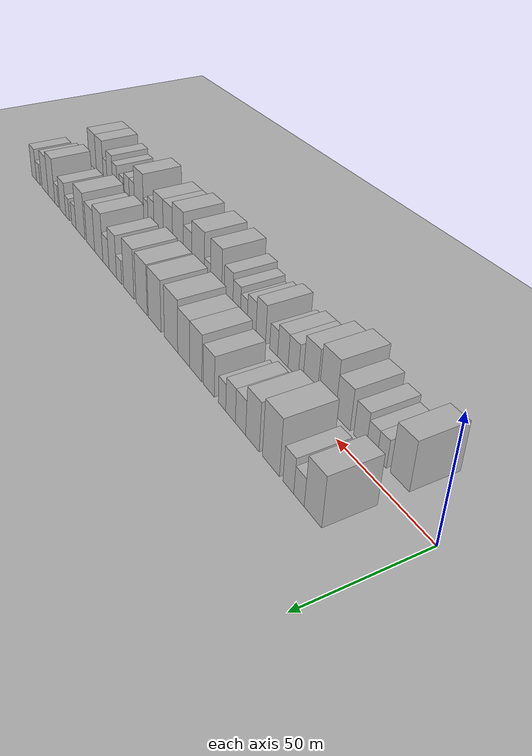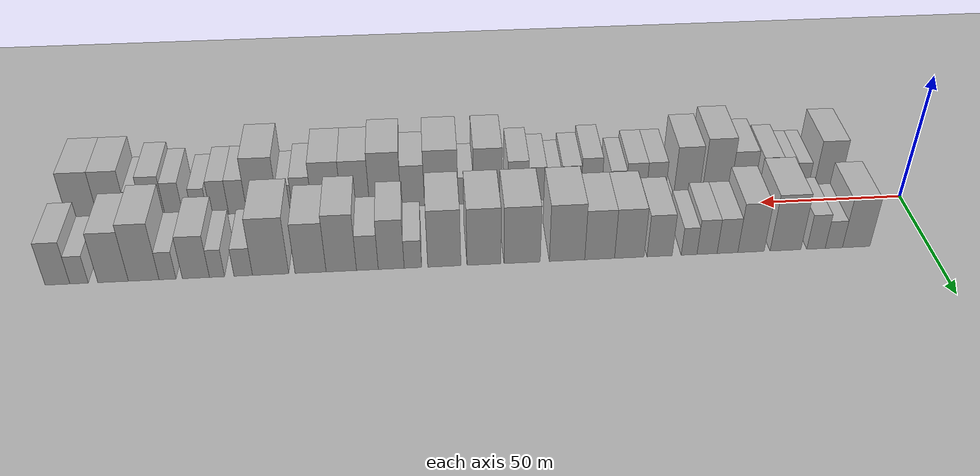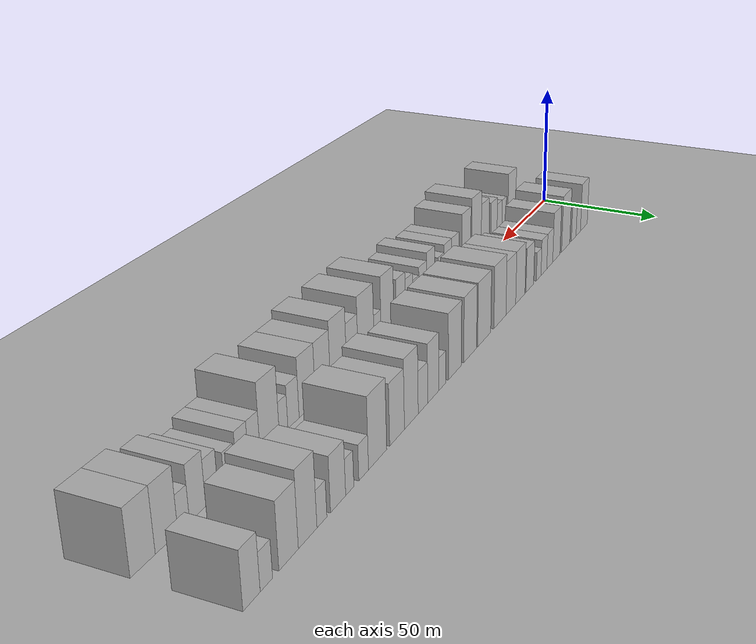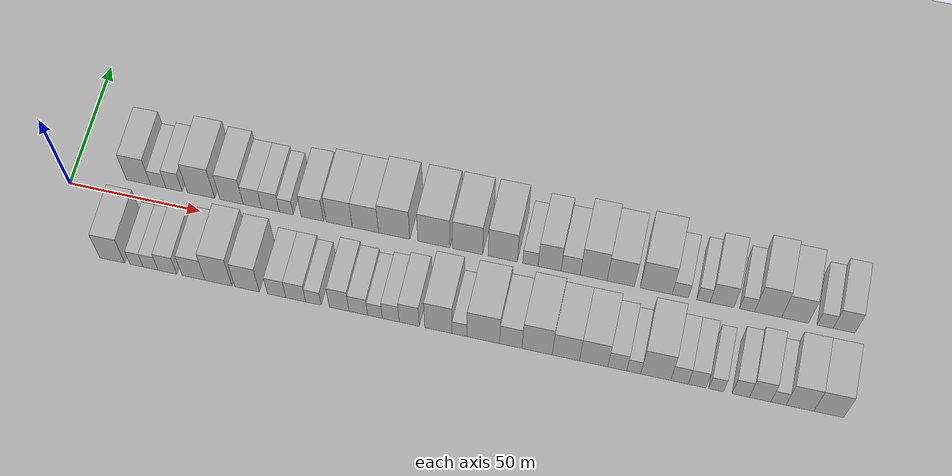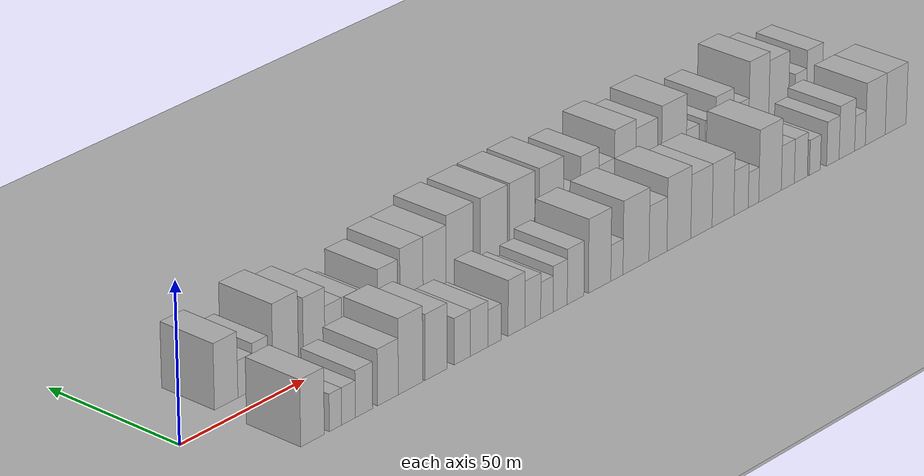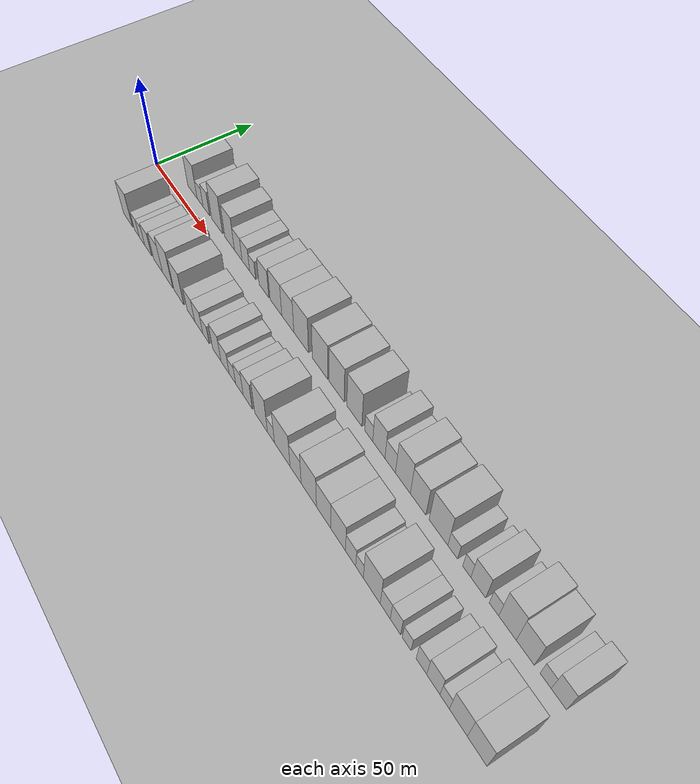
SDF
<?xml version="1.0" encoding="utf-8"?>

<sdf version="1.6">

   <world name="default">

      <gui fullscreen="0">

         <camera name="user_camera">

            <pose>-15 0 4.57585 0 0 0</pose>

            <view_controller>orbit</view_controller>

         </camera>

      </gui>

      <scene>

         <sky>

           <clouds>

             <speed>12</speed>

           </clouds>

         </sky>

         <ambient>0.4 0.4 0.4 1</ambient>

         <background>0.7 0.7 0.7 1</background>

         <shadows>1</shadows>

      </scene>

      <gravity>0 0 -9.8066</gravity>

      <magnetic_field>6e-06 2.3e-05 -4.2e-05</magnetic_field>

      <physics default="0" name="default_physics" type="ode">

         <ode>

            <solver>

               <type>quick</type>

               <iters>10</iters>

               <sor>1.0</sor>

               <use_dynamic_moi_rescaling>0</use_dynamic_moi_rescaling>

            </solver>

            <constraints>

               <cfm>0</cfm>

               <erp>0.2</erp>

               <contact_max_correcting_vel>100</contact_max_correcting_vel>

               <contact_surface_layer>0.001</contact_surface_layer>

            </constraints>

         </ode>

         <max_step_size>0.004</max_step_size>

         <real_time_factor>1</real_time_factor>

         <real_time_update_rate>250</real_time_update_rate>

      </physics>

      <light name="sun" type="directional">

         <cast_shadows>1</cast_shadows>

         <pose>0 0 10 0 0 0</pose>

         <diffuse>0.8 0.8 0.8 1</diffuse>

         <specular>0.2 0.2 0.2 1</specular>

         <attenuation>

            <range>1000</range>

            <constant>0.9</constant>

            <linear>0.01</linear>

            <quadratic>0.001</quadratic>

         </attenuation>

         <direction>-0.5 0.1 -0.9</direction>

      </light>

      <include>

         <name>ground_plane_1</name>

         <uri>model://HANNAS_ground_plane</uri>

         <pose>0 0 0  0 0 0</pose>

      </include>

      <include>

         <name>ground_plane_2</name>

         <uri>model://HANNAS_ground_plane</uri>

         <pose>100 0 0  0 0 0</pose>

      </include>

      <model name="building_1">

         <static>1</static>

         <pose frame="">24.6695 16.0000 0 0.000000 0.000000 1.570796</pose>

         <link name="link">

            <pose frame="">0 0 10.50 0 0 0</pose>

            <collision name="collision">

               <geometry>

                  <box>

                     <size>20.0000 9.3389 21.0000</size>

                  </box>

               </geometry>

               <max_contacts>10</max_contacts>

               <surface>

                  <contact>

                     <ode/>

                  </contact>

                  <bounce/>

                  <friction>

                     <torsional>

                        <ode/>

                     </torsional>

                     <ode/>

                  </friction>

               </surface>

            </collision>

            <visual name="visual">

               <cast_shadows>0</cast_shadows>

               <geometry>

                  <box>

                     <size>20.0000 9.3389 21.0000</size>

                  </box>

               </geometry>

               <material>

                  <script>

                     <uri>model://HANNAS_wall/materials/scripts</uri>

                     <uri>model://HANNAS_wall/materials/textures</uri>

                     <name>vrc/HANNAS_wall</name>

                  </script>

               </material>

            </visual>

            <self_collide>0</self_collide>

            <enable_wind>0</enable_wind>

            <kinematic>0</kinematic>

         </link>

      </model>

      <model name="building_2">

         <static>1</static>

         <pose frame="">32.2681 16.0000 0 0.000000 0.000000 1.570796</pose>

         <link name="link">

            <pose frame="">0 0 6.00 0 0 0</pose>

            <collision name="collision">

               <geometry>

                  <box>

                     <size>20.0000 5.8583 12.0000</size>

                  </box>

               </geometry>

               <max_contacts>10</max_contacts>

               <surface>

                  <contact>

                     <ode/>

                  </contact>

                  <bounce/>

                  <friction>

                     <torsional>

                        <ode/>

                     </torsional>

                     <ode/>

                  </friction>

               </surface>

            </collision>

            <visual name="visual">

               <cast_shadows>0</cast_shadows>

               <geometry>

                  <box>

                     <size>20.0000 5.8583 12.0000</size>

                  </box>

               </geometry>

               <material>

                  <script>

                     <uri>model://HANNAS_wall/materials/scripts</uri>

                     <uri>model://HANNAS_wall/materials/textures</uri>

                     <name>vrc/HANNAS_wall</name>

                  </script>

               </material>

            </visual>

            <self_collide>0</self_collide>

            <enable_wind>0</enable_wind>

            <kinematic>0</kinematic>

         </link>

      </model>

      <model name="building_3">

         <static>1</static>

         <pose frame="">38.3057 16.0000 0 0.000000 0.000000 1.570796</pose>

         <link name="link">

            <pose frame="">0 0 7.50 0 0 0</pose>

            <collision name="collision">

               <geometry>

                  <box>

                     <size>20.0000 6.2168 15.0000</size>

                  </box>

               </geometry>

               <max_contacts>10</max_contacts>

               <surface>

                  <contact>

                     <ode/>

                  </contact>

                  <bounce/>

                  <friction>

                     <torsional>

                        <ode/>

                     </torsional>

                     <ode/>

                  </friction>

               </surface>

            </collision>

            <visual name="visual">

               <cast_shadows>0</cast_shadows>

               <geometry>

                  <box>

                     <size>20.0000 6.2168 15.0000</size>

                  </box>

               </geometry>

               <material>

                  <script>

                     <uri>model://HANNAS_wall/materials/scripts</uri>

                     <uri>model://HANNAS_wall/materials/textures</uri>

                     <name>vrc/HANNAS_wall</name>

                  </script>

               </material>

            </visual>

            <self_collide>0</self_collide>

            <enable_wind>0</enable_wind>

            <kinematic>0</kinematic>

         </link>

      </model>

      <model name="building_4">

         <static>1</static>

         <pose frame="">48.6294 16.0000 0 0.000000 0.000000 1.570796</pose>

         <link name="link">

            <pose frame="">0 0 12.00 0 0 0</pose>

            <collision name="collision">

               <geometry>

                  <box>

                     <size>20.0000 10.4307 24.0000</size>

                  </box>

               </geometry>

               <max_contacts>10</max_contacts>

               <surface>

                  <contact>

                     <ode/>

                  </contact>

                  <bounce/>

                  <friction>

                     <torsional>

                        <ode/>

                     </torsional>

                     <ode/>

                  </friction>

               </surface>

            </collision>

            <visual name="visual">

               <cast_shadows>0</cast_shadows>

               <geometry>

                  <box>

                     <size>20.0000 10.4307 24.0000</size>

                  </box>

               </geometry>

               <material>

                  <script>

                     <uri>model://HANNAS_wall/materials/scripts</uri>

                     <uri>model://HANNAS_wall/materials/textures</uri>

                     <name>vrc/HANNAS_wall</name>

                  </script>

               </material>

            </visual>

            <self_collide>0</self_collide>

            <enable_wind>0</enable_wind>

            <kinematic>0</kinematic>

         </link>

      </model>

      <model name="building_5">

         <static>1</static>

         <pose frame="">60.2701 16.0000 0 0.000000 0.000000 1.570796</pose>

         <link name="link">

            <pose frame="">0 0 10.50 0 0 0</pose>

            <collision name="collision">

               <geometry>

                  <box>

                     <size>20.0000 8.8506 21.0000</size>

                  </box>

               </geometry>

               <max_contacts>10</max_contacts>

               <surface>

                  <contact>

                     <ode/>

                  </contact>

                  <bounce/>

                  <friction>

                     <torsional>

                        <ode/>

                     </torsional>

                     <ode/>

                  </friction>

               </surface>

            </collision>

            <visual name="visual">

               <cast_shadows>0</cast_shadows>

               <geometry>

                  <box>

                     <size>20.0000 8.8506 21.0000</size>

                  </box>

               </geometry>

               <material>

                  <script>

                     <uri>model://HANNAS_wall/materials/scripts</uri>

                     <uri>model://HANNAS_wall/materials/textures</uri>

                     <name>vrc/HANNAS_wall</name>

                  </script>

               </material>

            </visual>

            <self_collide>0</self_collide>

            <enable_wind>0</enable_wind>

            <kinematic>0</kinematic>

         </link>

      </model>

      <model name="building_6">

         <static>1</static>

         <pose frame="">68.1746 16.0000 0 0.000000 0.000000 1.570796</pose>

         <link name="link">

            <pose frame="">0 0 7.50 0 0 0</pose>

            <collision name="collision">

               <geometry>

                  <box>

                     <size>20.0000 6.9584 15.0000</size>

                  </box>

               </geometry>

               <max_contacts>10</max_contacts>

               <surface>

                  <contact>

                     <ode/>

                  </contact>

                  <bounce/>

                  <friction>

                     <torsional>

                        <ode/>

                     </torsional>

                     <ode/>

                  </friction>

               </surface>

            </collision>

            <visual name="visual">

               <cast_shadows>0</cast_shadows>

               <geometry>

                  <box>

                     <size>20.0000 6.9584 15.0000</size>

                  </box>

               </geometry>

               <material>

                  <script>

                     <uri>model://HANNAS_wall/materials/scripts</uri>

                     <uri>model://HANNAS_wall/materials/textures</uri>

                     <name>vrc/HANNAS_wall</name>

                  </script>

               </material>

            </visual>

            <self_collide>0</self_collide>

            <enable_wind>0</enable_wind>

            <kinematic>0</kinematic>

         </link>

      </model>

      <model name="building_7">

         <static>1</static>

         <pose frame="">75.0255 16.0000 0 0.000000 0.000000 1.570796</pose>

         <link name="link">

            <pose frame="">0 0 7.50 0 0 0</pose>

            <collision name="collision">

               <geometry>

                  <box>

                     <size>20.0000 6.7435 15.0000</size>

                  </box>

               </geometry>

               <max_contacts>10</max_contacts>

               <surface>

                  <contact>

                     <ode/>

                  </contact>

                  <bounce/>

                  <friction>

                     <torsional>

                        <ode/>

                     </torsional>

                     <ode/>

                  </friction>

               </surface>

            </collision>

            <visual name="visual">

               <cast_shadows>0</cast_shadows>

               <geometry>

                  <box>

                     <size>20.0000 6.7435 15.0000</size>

                  </box>

               </geometry>

               <material>

                  <script>

                     <uri>model://HANNAS_wall/materials/scripts</uri>

                     <uri>model://HANNAS_wall/materials/textures</uri>

                     <name>vrc/HANNAS_wall</name>

                  </script>

               </material>

            </visual>

            <self_collide>0</self_collide>

            <enable_wind>0</enable_wind>

            <kinematic>0</kinematic>

         </link>

      </model>

      <model name="building_8">

         <static>1</static>

         <pose frame="">81.0402 16.0000 0 0.000000 0.000000 1.570796</pose>

         <link name="link">

            <pose frame="">0 0 6.00 0 0 0</pose>

            <collision name="collision">

               <geometry>

                  <box>

                     <size>20.0000 5.2859 12.0000</size>

                  </box>

               </geometry>

               <max_contacts>10</max_contacts>

               <surface>

                  <contact>

                     <ode/>

                  </contact>

                  <bounce/>

                  <friction>

                     <torsional>

                        <ode/>

                     </torsional>

                     <ode/>

                  </friction>

               </surface>

            </collision>

            <visual name="visual">

               <cast_shadows>0</cast_shadows>

               <geometry>

                  <box>

                     <size>20.0000 5.2859 12.0000</size>

                  </box>

               </geometry>

               <material>

                  <script>

                     <uri>model://HANNAS_wall/materials/scripts</uri>

                     <uri>model://HANNAS_wall/materials/textures</uri>

                     <name>vrc/HANNAS_wall</name>

                  </script>

               </material>

            </visual>

            <self_collide>0</self_collide>

            <enable_wind>0</enable_wind>

            <kinematic>0</kinematic>

         </link>

      </model>

      <model name="building_9">

         <static>1</static>

         <pose frame="">90.8929 16.0000 0 0.000000 0.000000 1.570796</pose>

         <link name="link">

            <pose frame="">0 0 9.00 0 0 0</pose>

            <collision name="collision">

               <geometry>

                  <box>

                     <size>20.0000 8.4196 18.0000</size>

                  </box>

               </geometry>

               <max_contacts>10</max_contacts>

               <surface>

                  <contact>

                     <ode/>

                  </contact>

                  <bounce/>

                  <friction>

                     <torsional>

                        <ode/>

                     </torsional>

                     <ode/>

                  </friction>

               </surface>

            </collision>

            <visual name="visual">

               <cast_shadows>0</cast_shadows>

               <geometry>

                  <box>

                     <size>20.0000 8.4196 18.0000</size>

                  </box>

               </geometry>

               <material>

                  <script>

                     <uri>model://HANNAS_wall/materials/scripts</uri>

                     <uri>model://HANNAS_wall/materials/textures</uri>

                     <name>vrc/HANNAS_wall</name>

                  </script>

               </material>

            </visual>

            <self_collide>0</self_collide>

            <enable_wind>0</enable_wind>

            <kinematic>0</kinematic>

         </link>

      </model>

      <model name="building_10">

         <static>1</static>

         <pose frame="">100.9923 16.0000 0 0.000000 0.000000 1.570796</pose>

         <link name="link">

            <pose frame="">0 0 10.50 0 0 0</pose>

            <collision name="collision">

               <geometry>

                  <box>

                     <size>20.0000 9.7791 21.0000</size>

                  </box>

               </geometry>

               <max_contacts>10</max_contacts>

               <surface>

                  <contact>

                     <ode/>

                  </contact>

                  <bounce/>

                  <friction>

                     <torsional>

                        <ode/>

                     </torsional>

                     <ode/>

                  </friction>

               </surface>

            </collision>

            <visual name="visual">

               <cast_shadows>0</cast_shadows>

               <geometry>

                  <box>

                     <size>20.0000 9.7791 21.0000</size>

                  </box>

               </geometry>

               <material>

                  <script>

                     <uri>model://HANNAS_wall/materials/scripts</uri>

                     <uri>model://HANNAS_wall/materials/textures</uri>

                     <name>vrc/HANNAS_wall</name>

                  </script>

               </material>

            </visual>

            <self_collide>0</self_collide>

            <enable_wind>0</enable_wind>

            <kinematic>0</kinematic>

         </link>

      </model>

      <model name="building_11">

         <static>1</static>

         <pose frame="">110.8276 16.0000 0 0.000000 0.000000 1.570796</pose>

         <link name="link">

            <pose frame="">0 0 10.50 0 0 0</pose>

            <collision name="collision">

               <geometry>

                  <box>

                     <size>20.0000 9.8916 21.0000</size>

                  </box>

               </geometry>

               <max_contacts>10</max_contacts>

               <surface>

                  <contact>

                     <ode/>

                  </contact>

                  <bounce/>

                  <friction>

                     <torsional>

                        <ode/>

                     </torsional>

                     <ode/>

                  </friction>

               </surface>

            </collision>

            <visual name="visual">

               <cast_shadows>0</cast_shadows>

               <geometry>

                  <box>

                     <size>20.0000 9.8916 21.0000</size>

                  </box>

               </geometry>

               <material>

                  <script>

                     <uri>model://HANNAS_wall/materials/scripts</uri>

                     <uri>model://HANNAS_wall/materials/textures</uri>

                     <name>vrc/HANNAS_wall</name>

                  </script>

               </material>

            </visual>

            <self_collide>0</self_collide>

            <enable_wind>0</enable_wind>

            <kinematic>0</kinematic>

         </link>

      </model>

      <model name="building_12">

         <static>1</static>

         <pose frame="">121.6215 16.0000 0 0.000000 0.000000 1.570796</pose>

         <link name="link">

            <pose frame="">0 0 12.00 0 0 0</pose>

            <collision name="collision">

               <geometry>

                  <box>

                     <size>20.0000 11.6962 24.0000</size>

                  </box>

               </geometry>

               <max_contacts>10</max_contacts>

               <surface>

                  <contact>

                     <ode/>

                  </contact>

                  <bounce/>

                  <friction>

                     <torsional>

                        <ode/>

                     </torsional>

                     <ode/>

                  </friction>

               </surface>

            </collision>

            <visual name="visual">

               <cast_shadows>0</cast_shadows>

               <geometry>

                  <box>

                     <size>20.0000 11.6962 24.0000</size>

                  </box>

               </geometry>

               <material>

                  <script>

                     <uri>model://HANNAS_wall/materials/scripts</uri>

                     <uri>model://HANNAS_wall/materials/textures</uri>

                     <name>vrc/HANNAS_wall</name>

                  </script>

               </material>

            </visual>

            <self_collide>0</self_collide>

            <enable_wind>0</enable_wind>

            <kinematic>0</kinematic>

         </link>

      </model>

      <model name="building_13">

         <static>1</static>

         <pose frame="">136.4269 16.0000 0 0.000000 0.000000 1.570796</pose>

         <link name="link">

            <pose frame="">0 0 12.00 0 0 0</pose>

            <collision name="collision">

               <geometry>

                  <box>

                     <size>20.0000 11.9147 24.0000</size>

                  </box>

               </geometry>

               <max_contacts>10</max_contacts>

               <surface>

                  <contact>

                     <ode/>

                  </contact>

                  <bounce/>

                  <friction>

                     <torsional>

                        <ode/>

                     </torsional>

                     <ode/>

                  </friction>

               </surface>

            </collision>

            <visual name="visual">

               <cast_shadows>0</cast_shadows>

               <geometry>

                  <box>

                     <size>20.0000 11.9147 24.0000</size>

                  </box>

               </geometry>

               <material>

                  <script>

                     <uri>model://HANNAS_wall/materials/scripts</uri>

                     <uri>model://HANNAS_wall/materials/textures</uri>

                     <name>vrc/HANNAS_wall</name>

                  </script>

               </material>

            </visual>

            <self_collide>0</self_collide>

            <enable_wind>0</enable_wind>

            <kinematic>0</kinematic>

         </link>

      </model>

      <model name="building_14">

         <static>1</static>

         <pose frame="">148.9471 16.0000 0 0.000000 0.000000 1.570796</pose>

         <link name="link">

            <pose frame="">0 0 12.00 0 0 0</pose>

            <collision name="collision">

               <geometry>

                  <box>

                     <size>20.0000 11.1258 24.0000</size>

                  </box>

               </geometry>

               <max_contacts>10</max_contacts>

               <surface>

                  <contact>

                     <ode/>

                  </contact>

                  <bounce/>

                  <friction>

                     <torsional>

                        <ode/>

                     </torsional>

                     <ode/>

                  </friction>

               </surface>

            </collision>

            <visual name="visual">

               <cast_shadows>0</cast_shadows>

               <geometry>

                  <box>

                     <size>20.0000 11.1258 24.0000</size>

                  </box>

               </geometry>

               <material>

                  <script>

                     <uri>model://HANNAS_wall/materials/scripts</uri>

                     <uri>model://HANNAS_wall/materials/textures</uri>

                     <name>vrc/HANNAS_wall</name>

                  </script>

               </material>

            </visual>

            <self_collide>0</self_collide>

            <enable_wind>0</enable_wind>

            <kinematic>0</kinematic>

         </link>

      </model>

      <model name="building_15">

         <static>1</static>

         <pose frame="">161.9181 16.0000 0 0.000000 0.000000 1.570796</pose>

         <link name="link">

            <pose frame="">0 0 12.00 0 0 0</pose>

            <collision name="collision">

               <geometry>

                  <box>

                     <size>20.0000 10.8161 24.0000</size>

                  </box>

               </geometry>

               <max_contacts>10</max_contacts>

               <surface>

                  <contact>

                     <ode/>

                  </contact>

                  <bounce/>

                  <friction>

                     <torsional>

                        <ode/>

                     </torsional>

                     <ode/>

                  </friction>

               </surface>

            </collision>

            <visual name="visual">

               <cast_shadows>0</cast_shadows>

               <geometry>

                  <box>

                     <size>20.0000 10.8161 24.0000</size>

                  </box>

               </geometry>

               <material>

                  <script>

                     <uri>model://HANNAS_wall/materials/scripts</uri>

                     <uri>model://HANNAS_wall/materials/textures</uri>

                     <name>vrc/HANNAS_wall</name>

                  </script>

               </material>

            </visual>

            <self_collide>0</self_collide>

            <enable_wind>0</enable_wind>

            <kinematic>0</kinematic>

         </link>

      </model>

      <model name="building_16">

         <static>1</static>

         <pose frame="">172.1566 16.0000 0 0.000000 0.000000 1.570796</pose>

         <link name="link">

            <pose frame="">0 0 6.00 0 0 0</pose>

            <collision name="collision">

               <geometry>

                  <box>

                     <size>20.0000 5.6610 12.0000</size>

                  </box>

               </geometry>

               <max_contacts>10</max_contacts>

               <surface>

                  <contact>

                     <ode/>

                  </contact>

                  <bounce/>

                  <friction>

                     <torsional>

                        <ode/>

                     </torsional>

                     <ode/>

                  </friction>

               </surface>

            </collision>

            <visual name="visual">

               <cast_shadows>0</cast_shadows>

               <geometry>

                  <box>

                     <size>20.0000 5.6610 12.0000</size>

                  </box>

               </geometry>

               <material>

                  <script>

                     <uri>model://HANNAS_wall/materials/scripts</uri>

                     <uri>model://HANNAS_wall/materials/textures</uri>

                     <name>vrc/HANNAS_wall</name>

                  </script>

               </material>

            </visual>

            <self_collide>0</self_collide>

            <enable_wind>0</enable_wind>

            <kinematic>0</kinematic>

         </link>

      </model>

      <model name="building_17">

         <static>1</static>

         <pose frame="">179.1980 16.0000 0 0.000000 0.000000 1.570796</pose>

         <link name="link">

            <pose frame="">0 0 10.50 0 0 0</pose>

            <collision name="collision">

               <geometry>

                  <box>

                     <size>20.0000 8.4216 21.0000</size>

                  </box>

               </geometry>

               <max_contacts>10</max_contacts>

               <surface>

                  <contact>

                     <ode/>

                  </contact>

                  <bounce/>

                  <friction>

                     <torsional>

                        <ode/>

                     </torsional>

                     <ode/>

                  </friction>

               </surface>

            </collision>

            <visual name="visual">

               <cast_shadows>0</cast_shadows>

               <geometry>

                  <box>

                     <size>20.0000 8.4216 21.0000</size>

                  </box>

               </geometry>

               <material>

                  <script>

                     <uri>model://HANNAS_wall/materials/scripts</uri>

                     <uri>model://HANNAS_wall/materials/textures</uri>

                     <name>vrc/HANNAS_wall</name>

                  </script>

               </material>

            </visual>

            <self_collide>0</self_collide>

            <enable_wind>0</enable_wind>

            <kinematic>0</kinematic>

         </link>

      </model>

      <model name="building_18">

         <static>1</static>

         <pose frame="">186.9294 16.0000 0 0.000000 0.000000 1.570796</pose>

         <link name="link">

            <pose frame="">0 0 7.50 0 0 0</pose>

            <collision name="collision">

               <geometry>

                  <box>

                     <size>20.0000 7.0414 15.0000</size>

                  </box>

               </geometry>

               <max_contacts>10</max_contacts>

               <surface>

                  <contact>

                     <ode/>

                  </contact>

                  <bounce/>

                  <friction>

                     <torsional>

                        <ode/>

                     </torsional>

                     <ode/>

                  </friction>

               </surface>

            </collision>

            <visual name="visual">

               <cast_shadows>0</cast_shadows>

               <geometry>

                  <box>

                     <size>20.0000 7.0414 15.0000</size>

                  </box>

               </geometry>

               <material>

                  <script>

                     <uri>model://HANNAS_wall/materials/scripts</uri>

                     <uri>model://HANNAS_wall/materials/textures</uri>

                     <name>vrc/HANNAS_wall</name>

                  </script>

               </material>

            </visual>

            <self_collide>0</self_collide>

            <enable_wind>0</enable_wind>

            <kinematic>0</kinematic>

         </link>

      </model>

      <model name="building_19">

         <static>1</static>

         <pose frame="">195.3550 16.0000 0 0.000000 0.000000 1.570796</pose>

         <link name="link">

            <pose frame="">0 0 12.00 0 0 0</pose>

            <collision name="collision">

               <geometry>

                  <box>

                     <size>20.0000 9.8097 24.0000</size>

                  </box>

               </geometry>

               <max_contacts>10</max_contacts>

               <surface>

                  <contact>

                     <ode/>

                  </contact>

                  <bounce/>

                  <friction>

                     <torsional>

                        <ode/>

                     </torsional>

                     <ode/>

                  </friction>

               </surface>

            </collision>

            <visual name="visual">

               <cast_shadows>0</cast_shadows>

               <geometry>

                  <box>

                     <size>20.0000 9.8097 24.0000</size>

                  </box>

               </geometry>

               <material>

                  <script>

                     <uri>model://HANNAS_wall/materials/scripts</uri>

                     <uri>model://HANNAS_wall/materials/textures</uri>

                     <name>vrc/HANNAS_wall</name>

                  </script>

               </material>

            </visual>

            <self_collide>0</self_collide>

            <enable_wind>0</enable_wind>

            <kinematic>0</kinematic>

         </link>

      </model>

      <model name="building_20">

         <static>1</static>

         <pose frame="">205.2754 16.0000 0 0.000000 0.000000 1.570796</pose>

         <link name="link">

            <pose frame="">0 0 10.50 0 0 0</pose>

            <collision name="collision">

               <geometry>

                  <box>

                     <size>20.0000 10.0312 21.0000</size>

                  </box>

               </geometry>

               <max_contacts>10</max_contacts>

               <surface>

                  <contact>

                     <ode/>

                  </contact>

                  <bounce/>

                  <friction>

                     <torsional>

                        <ode/>

                     </torsional>

                     <ode/>

                  </friction>

               </surface>

            </collision>

            <visual name="visual">

               <cast_shadows>0</cast_shadows>

               <geometry>

                  <box>

                     <size>20.0000 10.0312 21.0000</size>

                  </box>

               </geometry>

               <material>

                  <script>

                     <uri>model://HANNAS_wall/materials/scripts</uri>

                     <uri>model://HANNAS_wall/materials/textures</uri>

                     <name>vrc/HANNAS_wall</name>

                  </script>

               </material>

            </visual>

            <self_collide>0</self_collide>

            <enable_wind>0</enable_wind>

            <kinematic>0</kinematic>

         </link>

      </model>

      <model name="building_21">

         <static>1</static>

         <pose frame="">218.1101 16.0000 0 0.000000 0.000000 1.570796</pose>

         <link name="link">

            <pose frame="">0 0 12.00 0 0 0</pose>

            <collision name="collision">

               <geometry>

                  <box>

                     <size>20.0000 11.6382 24.0000</size>

                  </box>

               </geometry>

               <max_contacts>10</max_contacts>

               <surface>

                  <contact>

                     <ode/>

                  </contact>

                  <bounce/>

                  <friction>

                     <torsional>

                        <ode/>

                     </torsional>

                     <ode/>

                  </friction>

               </surface>

            </collision>

            <visual name="visual">

               <cast_shadows>0</cast_shadows>

               <geometry>

                  <box>

                     <size>20.0000 11.6382 24.0000</size>

                  </box>

               </geometry>

               <material>

                  <script>

                     <uri>model://HANNAS_wall/materials/scripts</uri>

                     <uri>model://HANNAS_wall/materials/textures</uri>

                     <name>vrc/HANNAS_wall</name>

                  </script>

               </material>

            </visual>

            <self_collide>0</self_collide>

            <enable_wind>0</enable_wind>

            <kinematic>0</kinematic>

         </link>

      </model>

      <model name="building_22">

         <static>1</static>

         <pose frame="">226.8949 16.0000 0 0.000000 0.000000 1.570796</pose>

         <link name="link">

            <pose frame="">0 0 6.00 0 0 0</pose>

            <collision name="collision">

               <geometry>

                  <box>

                     <size>20.0000 5.9314 12.0000</size>

                  </box>

               </geometry>

               <max_contacts>10</max_contacts>

               <surface>

                  <contact>

                     <ode/>

                  </contact>

                  <bounce/>

                  <friction>

                     <torsional>

                        <ode/>

                     </torsional>

                     <ode/>

                  </friction>

               </surface>

            </collision>

            <visual name="visual">

               <cast_shadows>0</cast_shadows>

               <geometry>

                  <box>

                     <size>20.0000 5.9314 12.0000</size>

                  </box>

               </geometry>

               <material>

                  <script>

                     <uri>model://HANNAS_wall/materials/scripts</uri>

                     <uri>model://HANNAS_wall/materials/textures</uri>

                     <name>vrc/HANNAS_wall</name>

                  </script>

               </material>

            </visual>

            <self_collide>0</self_collide>

            <enable_wind>0</enable_wind>

            <kinematic>0</kinematic>

         </link>

      </model>

      <model name="building_23">

         <static>1</static>

         <pose frame="">235.2783 16.0000 0 0.000000 0.000000 1.570796</pose>

         <link name="link">

            <pose frame="">0 0 6.00 0 0 0</pose>

            <collision name="collision">

               <geometry>

                  <box>

                     <size>20.0000 4.8353 12.0000</size>

                  </box>

               </geometry>

               <max_contacts>10</max_contacts>

               <surface>

                  <contact>

                     <ode/>

                  </contact>

                  <bounce/>

                  <friction>

                     <torsional>

                        <ode/>

                     </torsional>

                     <ode/>

                  </friction>

               </surface>

            </collision>

            <visual name="visual">

               <cast_shadows>0</cast_shadows>

               <geometry>

                  <box>

                     <size>20.0000 4.8353 12.0000</size>

                  </box>

               </geometry>

               <material>

                  <script>

                     <uri>model://HANNAS_wall/materials/scripts</uri>

                     <uri>model://HANNAS_wall/materials/textures</uri>

                     <name>vrc/HANNAS_wall</name>

                  </script>

               </material>

            </visual>

            <self_collide>0</self_collide>

            <enable_wind>0</enable_wind>

            <kinematic>0</kinematic>

         </link>

      </model>

      <model name="building_24">

         <static>1</static>

         <pose frame="">242.0140 16.0000 0 0.000000 0.000000 1.570796</pose>

         <link name="link">

            <pose frame="">0 0 9.00 0 0 0</pose>

            <collision name="collision">

               <geometry>

                  <box>

                     <size>20.0000 8.6360 18.0000</size>

                  </box>

               </geometry>

               <max_contacts>10</max_contacts>

               <surface>

                  <contact>

                     <ode/>

                  </contact>

                  <bounce/>

                  <friction>

                     <torsional>

                        <ode/>

                     </torsional>

                     <ode/>

                  </friction>

               </surface>

            </collision>

            <visual name="visual">

               <cast_shadows>0</cast_shadows>

               <geometry>

                  <box>

                     <size>20.0000 8.6360 18.0000</size>

                  </box>

               </geometry>

               <material>

                  <script>

                     <uri>model://HANNAS_wall/materials/scripts</uri>

                     <uri>model://HANNAS_wall/materials/textures</uri>

                     <name>vrc/HANNAS_wall</name>

                  </script>

               </material>

            </visual>

            <self_collide>0</self_collide>

            <enable_wind>0</enable_wind>

            <kinematic>0</kinematic>

         </link>

      </model>

      <model name="building_25">

         <static>1</static>

         <pose frame="">251.0235 16.0000 0 0.000000 0.000000 1.570796</pose>

         <link name="link">

            <pose frame="">0 0 6.00 0 0 0</pose>

            <collision name="collision">

               <geometry>

                  <box>

                     <size>20.0000 5.3831 12.0000</size>

                  </box>

               </geometry>

               <max_contacts>10</max_contacts>

               <surface>

                  <contact>

                     <ode/>

                  </contact>

                  <bounce/>

                  <friction>

                     <torsional>

                        <ode/>

                     </torsional>

                     <ode/>

                  </friction>

               </surface>

            </collision>

            <visual name="visual">

               <cast_shadows>0</cast_shadows>

               <geometry>

                  <box>

                     <size>20.0000 5.3831 12.0000</size>

                  </box>

               </geometry>

               <material>

                  <script>

                     <uri>model://HANNAS_wall/materials/scripts</uri>

                     <uri>model://HANNAS_wall/materials/textures</uri>

                     <name>vrc/HANNAS_wall</name>

                  </script>

               </material>

            </visual>

            <self_collide>0</self_collide>

            <enable_wind>0</enable_wind>

            <kinematic>0</kinematic>

         </link>

      </model>

      <model name="building_26">

         <static>1</static>

         <pose frame="">258.5705 16.0000 0 0.000000 0.000000 1.570796</pose>

         <link name="link">

            <pose frame="">0 0 12.00 0 0 0</pose>

            <collision name="collision">

               <geometry>

                  <box>

                     <size>20.0000 9.7108 24.0000</size>

                  </box>

               </geometry>

               <max_contacts>10</max_contacts>

               <surface>

                  <contact>

                     <ode/>

                  </contact>

                  <bounce/>

                  <friction>

                     <torsional>

                        <ode/>

                     </torsional>

                     <ode/>

                  </friction>

               </surface>

            </collision>

            <visual name="visual">

               <cast_shadows>0</cast_shadows>

               <geometry>

                  <box>

                     <size>20.0000 9.7108 24.0000</size>

                  </box>

               </geometry>

               <material>

                  <script>

                     <uri>model://HANNAS_wall/materials/scripts</uri>

                     <uri>model://HANNAS_wall/materials/textures</uri>

                     <name>vrc/HANNAS_wall</name>

                  </script>

               </material>

            </visual>

            <self_collide>0</self_collide>

            <enable_wind>0</enable_wind>

            <kinematic>0</kinematic>

         </link>

      </model>

      <model name="building_27">

         <static>1</static>

         <pose frame="">268.2614 16.0000 0 0.000000 0.000000 1.570796</pose>

         <link name="link">

            <pose frame="">0 0 10.50 0 0 0</pose>

            <collision name="collision">

               <geometry>

                  <box>

                     <size>20.0000 9.6710 21.0000</size>

                  </box>

               </geometry>

               <max_contacts>10</max_contacts>

               <surface>

                  <contact>

                     <ode/>

                  </contact>

                  <bounce/>

                  <friction>

                     <torsional>

                        <ode/>

                     </torsional>

                     <ode/>

                  </friction>

               </surface>

            </collision>

            <visual name="visual">

               <cast_shadows>0</cast_shadows>

               <geometry>

                  <box>

                     <size>20.0000 9.6710 21.0000</size>

                  </box>

               </geometry>

               <material>

                  <script>

                     <uri>model://HANNAS_wall/materials/scripts</uri>

                     <uri>model://HANNAS_wall/materials/textures</uri>

                     <name>vrc/HANNAS_wall</name>

                  </script>

               </material>

            </visual>

            <self_collide>0</self_collide>

            <enable_wind>0</enable_wind>

            <kinematic>0</kinematic>

         </link>

      </model>

      <model name="building_28">

         <static>1</static>

         <pose frame="">278.9911 16.0000 0 0.000000 0.000000 1.570796</pose>

         <link name="link">

            <pose frame="">0 0 6.00 0 0 0</pose>

            <collision name="collision">

               <geometry>

                  <box>

                     <size>20.0000 5.7886 12.0000</size>

                  </box>

               </geometry>

               <max_contacts>10</max_contacts>

               <surface>

                  <contact>

                     <ode/>

                  </contact>

                  <bounce/>

                  <friction>

                     <torsional>

                        <ode/>

                     </torsional>

                     <ode/>

                  </friction>

               </surface>

            </collision>

            <visual name="visual">

               <cast_shadows>0</cast_shadows>

               <geometry>

                  <box>

                     <size>20.0000 5.7886 12.0000</size>

                  </box>

               </geometry>

               <material>

                  <script>

                     <uri>model://HANNAS_wall/materials/scripts</uri>

                     <uri>model://HANNAS_wall/materials/textures</uri>

                     <name>vrc/HANNAS_wall</name>

                  </script>

               </material>

            </visual>

            <self_collide>0</self_collide>

            <enable_wind>0</enable_wind>

            <kinematic>0</kinematic>

         </link>

      </model>

      <model name="building_29">

         <static>1</static>

         <pose frame="">285.7840 16.0000 0 0.000000 0.000000 1.570796</pose>

         <link name="link">

            <pose frame="">0 0 9.00 0 0 0</pose>

            <collision name="collision">

               <geometry>

                  <box>

                     <size>20.0000 7.7971 18.0000</size>

                  </box>

               </geometry>

               <max_contacts>10</max_contacts>

               <surface>

                  <contact>

                     <ode/>

                  </contact>

                  <bounce/>

                  <friction>

                     <torsional>

                        <ode/>

                     </torsional>

                     <ode/>

                  </friction>

               </surface>

            </collision>

            <visual name="visual">

               <cast_shadows>0</cast_shadows>

               <geometry>

                  <box>

                     <size>20.0000 7.7971 18.0000</size>

                  </box>

               </geometry>

               <material>

                  <script>

                     <uri>model://HANNAS_wall/materials/scripts</uri>

                     <uri>model://HANNAS_wall/materials/textures</uri>

                     <name>vrc/HANNAS_wall</name>

                  </script>

               </material>

            </visual>

            <self_collide>0</self_collide>

            <enable_wind>0</enable_wind>

            <kinematic>0</kinematic>

         </link>

      </model>

      <model name="building_30">

         <static>1</static>

         <pose frame="">24.7320 -16.0000 0 0.000000 0.000000 1.570796</pose>

         <link name="link">

            <pose frame="">0 0 10.50 0 0 0</pose>

            <collision name="collision">

               <geometry>

                  <box>

                     <size>20.0000 9.4639 21.0000</size>

                  </box>

               </geometry>

               <max_contacts>10</max_contacts>

               <surface>

                  <contact>

                     <ode/>

                  </contact>

                  <bounce/>

                  <friction>

                     <torsional>

                        <ode/>

                     </torsional>

                     <ode/>

                  </friction>

               </surface>

            </collision>

            <visual name="visual">

               <cast_shadows>0</cast_shadows>

               <geometry>

                  <box>

                     <size>20.0000 9.4639 21.0000</size>

                  </box>

               </geometry>

               <material>

                  <script>

                     <uri>model://HANNAS_wall/materials/scripts</uri>

                     <uri>model://HANNAS_wall/materials/textures</uri>

                     <name>vrc/HANNAS_wall</name>

                  </script>

               </material>

            </visual>

            <self_collide>0</self_collide>

            <enable_wind>0</enable_wind>

            <kinematic>0</kinematic>

         </link>

      </model>

      <model name="building_31">

         <static>1</static>

         <pose frame="">33.9292 -16.0000 0 0.000000 0.000000 1.570796</pose>

         <link name="link">

            <pose frame="">0 0 6.00 0 0 0</pose>

            <collision name="collision">

               <geometry>

                  <box>

                     <size>20.0000 4.9306 12.0000</size>

                  </box>

               </geometry>

               <max_contacts>10</max_contacts>

               <surface>

                  <contact>

                     <ode/>

                  </contact>

                  <bounce/>

                  <friction>

                     <torsional>

                        <ode/>

                     </torsional>

                     <ode/>

                  </friction>

               </surface>

            </collision>

            <visual name="visual">

               <cast_shadows>0</cast_shadows>

               <geometry>

                  <box>

                     <size>20.0000 4.9306 12.0000</size>

                  </box>

               </geometry>

               <material>

                  <script>

                     <uri>model://HANNAS_wall/materials/scripts</uri>

                     <uri>model://HANNAS_wall/materials/textures</uri>

                     <name>vrc/HANNAS_wall</name>

                  </script>

               </material>

            </visual>

            <self_collide>0</self_collide>

            <enable_wind>0</enable_wind>

            <kinematic>0</kinematic>

         </link>

      </model>

      <model name="building_32">

         <static>1</static>

         <pose frame="">39.1990 -16.0000 0 0.000000 0.000000 1.570796</pose>

         <link name="link">

            <pose frame="">0 0 6.00 0 0 0</pose>

            <collision name="collision">

               <geometry>

                  <box>

                     <size>20.0000 5.6090 12.0000</size>

                  </box>

               </geometry>

               <max_contacts>10</max_contacts>

               <surface>

                  <contact>

                     <ode/>

                  </contact>

                  <bounce/>

                  <friction>

                     <torsional>

                        <ode/>

                     </torsional>

                     <ode/>

                  </friction>

               </surface>

            </collision>

            <visual name="visual">

               <cast_shadows>0</cast_shadows>

               <geometry>

                  <box>

                     <size>20.0000 5.6090 12.0000</size>

                  </box>

               </geometry>

               <material>

                  <script>

                     <uri>model://HANNAS_wall/materials/scripts</uri>

                     <uri>model://HANNAS_wall/materials/textures</uri>

                     <name>vrc/HANNAS_wall</name>

                  </script>

               </material>

            </visual>

            <self_collide>0</self_collide>

            <enable_wind>0</enable_wind>

            <kinematic>0</kinematic>

         </link>

      </model>

      <model name="building_33">

         <static>1</static>

         <pose frame="">45.5052 -16.0000 0 0.000000 0.000000 1.570796</pose>

         <link name="link">

            <pose frame="">0 0 7.50 0 0 0</pose>

            <collision name="collision">

               <geometry>

                  <box>

                     <size>20.0000 7.0035 15.0000</size>

                  </box>

               </geometry>

               <max_contacts>10</max_contacts>

               <surface>

                  <contact>

                     <ode/>

                  </contact>

                  <bounce/>

                  <friction>

                     <torsional>

                        <ode/>

                     </torsional>

                     <ode/>

                  </friction>

               </surface>

            </collision>

            <visual name="visual">

               <cast_shadows>0</cast_shadows>

               <geometry>

                  <box>

                     <size>20.0000 7.0035 15.0000</size>

                  </box>

               </geometry>

               <material>

                  <script>

                     <uri>model://HANNAS_wall/materials/scripts</uri>

                     <uri>model://HANNAS_wall/materials/textures</uri>

                     <name>vrc/HANNAS_wall</name>

                  </script>

               </material>

            </visual>

            <self_collide>0</self_collide>

            <enable_wind>0</enable_wind>

            <kinematic>0</kinematic>

         </link>

      </model>

      <model name="building_34">

         <static>1</static>

         <pose frame="">55.2797 -16.0000 0 0.000000 0.000000 1.570796</pose>

         <link name="link">

            <pose frame="">0 0 9.00 0 0 0</pose>

            <collision name="collision">

               <geometry>

                  <box>

                     <size>20.0000 8.5454 18.0000</size>

                  </box>

               </geometry>

               <max_contacts>10</max_contacts>

               <surface>

                  <contact>

                     <ode/>

                  </contact>

                  <bounce/>

                  <friction>

                     <torsional>

                        <ode/>

                     </torsional>

                     <ode/>

                  </friction>

               </surface>

            </collision>

            <visual name="visual">

               <cast_shadows>0</cast_shadows>

               <geometry>

                  <box>

                     <size>20.0000 8.5454 18.0000</size>

                  </box>

               </geometry>

               <material>

                  <script>

                     <uri>model://HANNAS_wall/materials/scripts</uri>

                     <uri>model://HANNAS_wall/materials/textures</uri>

                     <name>vrc/HANNAS_wall</name>

                  </script>

               </material>

            </visual>

            <self_collide>0</self_collide>

            <enable_wind>0</enable_wind>

            <kinematic>0</kinematic>

         </link>

      </model>

      <model name="building_35">

         <static>1</static>

         <pose frame="">64.5947 -16.0000 0 0.000000 0.000000 1.570796</pose>

         <link name="link">

            <pose frame="">0 0 12.00 0 0 0</pose>

            <collision name="collision">

               <geometry>

                  <box>

                     <size>20.0000 10.0847 24.0000</size>

                  </box>

               </geometry>

               <max_contacts>10</max_contacts>

               <surface>

                  <contact>

                     <ode/>

                  </contact>

                  <bounce/>

                  <friction>

                     <torsional>

                        <ode/>

                     </torsional>

                     <ode/>

                  </friction>

               </surface>

            </collision>

            <visual name="visual">

               <cast_shadows>0</cast_shadows>

               <geometry>

                  <box>

                     <size>20.0000 10.0847 24.0000</size>

                  </box>

               </geometry>

               <material>

                  <script>

                     <uri>model://HANNAS_wall/materials/scripts</uri>

                     <uri>model://HANNAS_wall/materials/textures</uri>

                     <name>vrc/HANNAS_wall</name>

                  </script>

               </material>

            </visual>

            <self_collide>0</self_collide>

            <enable_wind>0</enable_wind>

            <kinematic>0</kinematic>

         </link>

      </model>

      <model name="building_36">

         <static>1</static>

         <pose frame="">75.2171 -16.0000 0 0.000000 0.000000 1.570796</pose>

         <link name="link">

            <pose frame="">0 0 10.50 0 0 0</pose>

            <collision name="collision">

               <geometry>

                  <box>

                     <size>20.0000 9.1601 21.0000</size>

                  </box>

               </geometry>

               <max_contacts>10</max_contacts>

               <surface>

                  <contact>

                     <ode/>

                  </contact>

                  <bounce/>

                  <friction>

                     <torsional>

                        <ode/>

                     </torsional>

                     <ode/>

                  </friction>

               </surface>

            </collision>

            <visual name="visual">

               <cast_shadows>0</cast_shadows>

               <geometry>

                  <box>

                     <size>20.0000 9.1601 21.0000</size>

                  </box>

               </geometry>

               <material>

                  <script>

                     <uri>model://HANNAS_wall/materials/scripts</uri>

                     <uri>model://HANNAS_wall/materials/textures</uri>

                     <name>vrc/HANNAS_wall</name>

                  </script>

               </material>

            </visual>

            <self_collide>0</self_collide>

            <enable_wind>0</enable_wind>

            <kinematic>0</kinematic>

         </link>

      </model>

      <model name="building_37">

         <static>1</static>

         <pose frame="">86.2322 -16.0000 0 0.000000 0.000000 1.570796</pose>

         <link name="link">

            <pose frame="">0 0 7.50 0 0 0</pose>

            <collision name="collision">

               <geometry>

                  <box>

                     <size>20.0000 6.8702 15.0000</size>

                  </box>

               </geometry>

               <max_contacts>10</max_contacts>

               <surface>

                  <contact>

                     <ode/>

                  </contact>

                  <bounce/>

                  <friction>

                     <torsional>

                        <ode/>

                     </torsional>

                     <ode/>

                  </friction>

               </surface>

            </collision>

            <visual name="visual">

               <cast_shadows>0</cast_shadows>

               <geometry>

                  <box>

                     <size>20.0000 6.8702 15.0000</size>

                  </box>

               </geometry>

               <material>

                  <script>

                     <uri>model://HANNAS_wall/materials/scripts</uri>

                     <uri>model://HANNAS_wall/materials/textures</uri>

                     <name>vrc/HANNAS_wall</name>

                  </script>

               </material>

            </visual>

            <self_collide>0</self_collide>

            <enable_wind>0</enable_wind>

            <kinematic>0</kinematic>

         </link>

      </model>

      <model name="building_38">

         <static>1</static>

         <pose frame="">93.3093 -16.0000 0 0.000000 0.000000 1.570796</pose>

         <link name="link">

            <pose frame="">0 0 7.50 0 0 0</pose>

            <collision name="collision">

               <geometry>

                  <box>

                     <size>20.0000 7.2840 15.0000</size>

                  </box>

               </geometry>

               <max_contacts>10</max_contacts>

               <surface>

                  <contact>

                     <ode/>

                  </contact>

                  <bounce/>

                  <friction>

                     <torsional>

                        <ode/>

                     </torsional>

                     <ode/>

                  </friction>

               </surface>

            </collision>

            <visual name="visual">

               <cast_shadows>0</cast_shadows>

               <geometry>

                  <box>

                     <size>20.0000 7.2840 15.0000</size>

                  </box>

               </geometry>

               <material>

                  <script>

                     <uri>model://HANNAS_wall/materials/scripts</uri>

                     <uri>model://HANNAS_wall/materials/textures</uri>

                     <name>vrc/HANNAS_wall</name>

                  </script>

               </material>

            </visual>

            <self_collide>0</self_collide>

            <enable_wind>0</enable_wind>

            <kinematic>0</kinematic>

         </link>

      </model>

      <model name="building_39">

         <static>1</static>

         <pose frame="">99.8046 -16.0000 0 0.000000 0.000000 1.570796</pose>

         <link name="link">

            <pose frame="">0 0 6.00 0 0 0</pose>

            <collision name="collision">

               <geometry>

                  <box>

                     <size>20.0000 5.7067 12.0000</size>

                  </box>

               </geometry>

               <max_contacts>10</max_contacts>

               <surface>

                  <contact>

                     <ode/>

                  </contact>

                  <bounce/>

                  <friction>

                     <torsional>

                        <ode/>

                     </torsional>

                     <ode/>

                  </friction>

               </surface>

            </collision>

            <visual name="visual">

               <cast_shadows>0</cast_shadows>

               <geometry>

                  <box>

                     <size>20.0000 5.7067 12.0000</size>

                  </box>

               </geometry>

               <material>

                  <script>

                     <uri>model://HANNAS_wall/materials/scripts</uri>

                     <uri>model://HANNAS_wall/materials/textures</uri>

                     <name>vrc/HANNAS_wall</name>

                  </script>

               </material>

            </visual>

            <self_collide>0</self_collide>

            <enable_wind>0</enable_wind>

            <kinematic>0</kinematic>

         </link>

      </model>

      <model name="building_40">

         <static>1</static>

         <pose frame="">109.2795 -16.0000 0 0.000000 0.000000 1.570796</pose>

         <link name="link">

            <pose frame="">0 0 9.00 0 0 0</pose>

            <collision name="collision">

               <geometry>

                  <box>

                     <size>20.0000 7.2429 18.0000</size>

                  </box>

               </geometry>

               <max_contacts>10</max_contacts>

               <surface>

                  <contact>

                     <ode/>

                  </contact>

                  <bounce/>

                  <friction>

                     <torsional>

                        <ode/>

                     </torsional>

                     <ode/>

                  </friction>

               </surface>

            </collision>

            <visual name="visual">

               <cast_shadows>0</cast_shadows>

               <geometry>

                  <box>

                     <size>20.0000 7.2429 18.0000</size>

                  </box>

               </geometry>

               <material>

                  <script>

                     <uri>model://HANNAS_wall/materials/scripts</uri>

                     <uri>model://HANNAS_wall/materials/textures</uri>

                     <name>vrc/HANNAS_wall</name>

                  </script>

               </material>

            </visual>

            <self_collide>0</self_collide>

            <enable_wind>0</enable_wind>

            <kinematic>0</kinematic>

         </link>

      </model>

      <model name="building_41">

         <static>1</static>

         <pose frame="">116.3133 -16.0000 0 0.000000 0.000000 1.570796</pose>

         <link name="link">

            <pose frame="">0 0 7.50 0 0 0</pose>

            <collision name="collision">

               <geometry>

                  <box>

                     <size>20.0000 6.8247 15.0000</size>

                  </box>

               </geometry>

               <max_contacts>10</max_contacts>

               <surface>

                  <contact>

                     <ode/>

                  </contact>

                  <bounce/>

                  <friction>

                     <torsional>

                        <ode/>

                     </torsional>

                     <ode/>

                  </friction>

               </surface>

            </collision>

            <visual name="visual">

               <cast_shadows>0</cast_shadows>

               <geometry>

                  <box>

                     <size>20.0000 6.8247 15.0000</size>

                  </box>

               </geometry>

               <material>

                  <script>

                     <uri>model://HANNAS_wall/materials/scripts</uri>

                     <uri>model://HANNAS_wall/materials/textures</uri>

                     <name>vrc/HANNAS_wall</name>

                  </script>

               </material>

            </visual>

            <self_collide>0</self_collide>

            <enable_wind>0</enable_wind>

            <kinematic>0</kinematic>

         </link>

      </model>

      <model name="building_42">

         <static>1</static>

         <pose frame="">122.4159 -16.0000 0 0.000000 0.000000 1.570796</pose>

         <link name="link">

            <pose frame="">0 0 6.00 0 0 0</pose>

            <collision name="collision">

               <geometry>

                  <box>

                     <size>20.0000 5.3806 12.0000</size>

                  </box>

               </geometry>

               <max_contacts>10</max_contacts>

               <surface>

                  <contact>

                     <ode/>

                  </contact>

                  <bounce/>

                  <friction>

                     <torsional>

                        <ode/>

                     </torsional>

                     <ode/>

                  </friction>

               </surface>

            </collision>

            <visual name="visual">

               <cast_shadows>0</cast_shadows>

               <geometry>

                  <box>

                     <size>20.0000 5.3806 12.0000</size>

                  </box>

               </geometry>

               <material>

                  <script>

                     <uri>model://HANNAS_wall/materials/scripts</uri>

                     <uri>model://HANNAS_wall/materials/textures</uri>

                     <name>vrc/HANNAS_wall</name>

                  </script>

               </material>

            </visual>

            <self_collide>0</self_collide>

            <enable_wind>0</enable_wind>

            <kinematic>0</kinematic>

         </link>

      </model>

      <model name="building_43">

         <static>1</static>

         <pose frame="">128.2004 -16.0000 0 0.000000 0.000000 1.570796</pose>

         <link name="link">

            <pose frame="">0 0 7.50 0 0 0</pose>

            <collision name="collision">

               <geometry>

                  <box>

                     <size>20.0000 6.1882 15.0000</size>

                  </box>

               </geometry>

               <max_contacts>10</max_contacts>

               <surface>

                  <contact>

                     <ode/>

                  </contact>

                  <bounce/>

                  <friction>

                     <torsional>

                        <ode/>

                     </torsional>

                     <ode/>

                  </friction>

               </surface>

            </collision>

            <visual name="visual">

               <cast_shadows>0</cast_shadows>

               <geometry>

                  <box>

                     <size>20.0000 6.1882 15.0000</size>

                  </box>

               </geometry>

               <material>

                  <script>

                     <uri>model://HANNAS_wall/materials/scripts</uri>

                     <uri>model://HANNAS_wall/materials/textures</uri>

                     <name>vrc/HANNAS_wall</name>

                  </script>

               </material>

            </visual>

            <self_collide>0</self_collide>

            <enable_wind>0</enable_wind>

            <kinematic>0</kinematic>

         </link>

      </model>

      <model name="building_44">

         <static>1</static>

         <pose frame="">134.9628 -16.0000 0 0.000000 0.000000 1.570796</pose>

         <link name="link">

            <pose frame="">0 0 9.00 0 0 0</pose>

            <collision name="collision">

               <geometry>

                  <box>

                     <size>20.0000 7.3366 18.0000</size>

                  </box>

               </geometry>

               <max_contacts>10</max_contacts>

               <surface>

                  <contact>

                     <ode/>

                  </contact>

                  <bounce/>

                  <friction>

                     <torsional>

                        <ode/>

                     </torsional>

                     <ode/>

                  </friction>

               </surface>

            </collision>

            <visual name="visual">

               <cast_shadows>0</cast_shadows>

               <geometry>

                  <box>

                     <size>20.0000 7.3366 18.0000</size>

                  </box>

               </geometry>

               <material>

                  <script>

                     <uri>model://HANNAS_wall/materials/scripts</uri>

                     <uri>model://HANNAS_wall/materials/textures</uri>

                     <name>vrc/HANNAS_wall</name>

                  </script>

               </material>

            </visual>

            <self_collide>0</self_collide>

            <enable_wind>0</enable_wind>

            <kinematic>0</kinematic>

         </link>

      </model>

      <model name="building_45">

         <static>1</static>

         <pose frame="">145.6103 -16.0000 0 0.000000 0.000000 1.570796</pose>

         <link name="link">

            <pose frame="">0 0 12.00 0 0 0</pose>

            <collision name="collision">

               <geometry>

                  <box>

                     <size>20.0000 9.9585 24.0000</size>

                  </box>

               </geometry>

               <max_contacts>10</max_contacts>

               <surface>

                  <contact>

                     <ode/>

                  </contact>

                  <bounce/>

                  <friction>

                     <torsional>

                        <ode/>

                     </torsional>

                     <ode/>

                  </friction>

               </surface>

            </collision>

            <visual name="visual">

               <cast_shadows>0</cast_shadows>

               <geometry>

                  <box>

                     <size>20.0000 9.9585 24.0000</size>

                  </box>

               </geometry>

               <material>

                  <script>

                     <uri>model://HANNAS_wall/materials/scripts</uri>

                     <uri>model://HANNAS_wall/materials/textures</uri>

                     <name>vrc/HANNAS_wall</name>

                  </script>

               </material>

            </visual>

            <self_collide>0</self_collide>

            <enable_wind>0</enable_wind>

            <kinematic>0</kinematic>

         </link>

      </model>

      <model name="building_46">

         <static>1</static>

         <pose frame="">153.2941 -16.0000 0 0.000000 0.000000 1.570796</pose>

         <link name="link">

            <pose frame="">0 0 6.00 0 0 0</pose>

            <collision name="collision">

               <geometry>

                  <box>

                     <size>20.0000 5.4092 12.0000</size>

                  </box>

               </geometry>

               <max_contacts>10</max_contacts>

               <surface>

                  <contact>

                     <ode/>

                  </contact>

                  <bounce/>

                  <friction>

                     <torsional>

                        <ode/>

                     </torsional>

                     <ode/>

                  </friction>

               </surface>

            </collision>

            <visual name="visual">

               <cast_shadows>0</cast_shadows>

               <geometry>

                  <box>

                     <size>20.0000 5.4092 12.0000</size>

                  </box>

               </geometry>

               <material>

                  <script>

                     <uri>model://HANNAS_wall/materials/scripts</uri>

                     <uri>model://HANNAS_wall/materials/textures</uri>

                     <name>vrc/HANNAS_wall</name>

                  </script>

               </material>

            </visual>

            <self_collide>0</self_collide>

            <enable_wind>0</enable_wind>

            <kinematic>0</kinematic>

         </link>

      </model>

      <model name="building_47">

         <static>1</static>

         <pose frame="">161.8614 -16.0000 0 0.000000 0.000000 1.570796</pose>

         <link name="link">

            <pose frame="">0 0 12.00 0 0 0</pose>

            <collision name="collision">

               <geometry>

                  <box>

                     <size>20.0000 11.7254 24.0000</size>

                  </box>

               </geometry>

               <max_contacts>10</max_contacts>

               <surface>

                  <contact>

                     <ode/>

                  </contact>

                  <bounce/>

                  <friction>

                     <torsional>

                        <ode/>

                     </torsional>

                     <ode/>

                  </friction>

               </surface>

            </collision>

            <visual name="visual">

               <cast_shadows>0</cast_shadows>

               <geometry>

                  <box>

                     <size>20.0000 11.7254 24.0000</size>

                  </box>

               </geometry>

               <material>

                  <script>

                     <uri>model://HANNAS_wall/materials/scripts</uri>

                     <uri>model://HANNAS_wall/materials/textures</uri>

                     <name>vrc/HANNAS_wall</name>

                  </script>

               </material>

            </visual>

            <self_collide>0</self_collide>

            <enable_wind>0</enable_wind>

            <kinematic>0</kinematic>

         </link>

      </model>

      <model name="building_48">

         <static>1</static>

         <pose frame="">171.7860 -16.0000 0 0.000000 0.000000 1.570796</pose>

         <link name="link">

            <pose frame="">0 0 9.00 0 0 0</pose>

            <collision name="collision">

               <geometry>

                  <box>

                     <size>20.0000 8.1237 18.0000</size>

                  </box>

               </geometry>

               <max_contacts>10</max_contacts>

               <surface>

                  <contact>

                     <ode/>

                  </contact>

                  <bounce/>

                  <friction>

                     <torsional>

                        <ode/>

                     </torsional>

                     <ode/>

                  </friction>

               </surface>

            </collision>

            <visual name="visual">

               <cast_shadows>0</cast_shadows>

               <geometry>

                  <box>

                     <size>20.0000 8.1237 18.0000</size>

                  </box>

               </geometry>

               <material>

                  <script>

                     <uri>model://HANNAS_wall/materials/scripts</uri>

                     <uri>model://HANNAS_wall/materials/textures</uri>

                     <name>vrc/HANNAS_wall</name>

                  </script>

               </material>

            </visual>

            <self_collide>0</self_collide>

            <enable_wind>0</enable_wind>

            <kinematic>0</kinematic>

         </link>

      </model>

      <model name="building_49">

         <static>1</static>

         <pose frame="">181.3100 -16.0000 0 0.000000 0.000000 1.570796</pose>

         <link name="link">

            <pose frame="">0 0 12.00 0 0 0</pose>

            <collision name="collision">

               <geometry>

                  <box>

                     <size>20.0000 10.9243 24.0000</size>

                  </box>

               </geometry>

               <max_contacts>10</max_contacts>

               <surface>

                  <contact>

                     <ode/>

                  </contact>

                  <bounce/>

                  <friction>

                     <torsional>

                        <ode/>

                     </torsional>

                     <ode/>

                  </friction>

               </surface>

            </collision>

            <visual name="visual">

               <cast_shadows>0</cast_shadows>

               <geometry>

                  <box>

                     <size>20.0000 10.9243 24.0000</size>

                  </box>

               </geometry>

               <material>

                  <script>

                     <uri>model://HANNAS_wall/materials/scripts</uri>

                     <uri>model://HANNAS_wall/materials/textures</uri>

                     <name>vrc/HANNAS_wall</name>

                  </script>

               </material>

            </visual>

            <self_collide>0</self_collide>

            <enable_wind>0</enable_wind>

            <kinematic>0</kinematic>

         </link>

      </model>

      <model name="building_50">

         <static>1</static>

         <pose frame="">191.6670 -16.0000 0 0.000000 0.000000 1.570796</pose>

         <link name="link">

            <pose frame="">0 0 10.50 0 0 0</pose>

            <collision name="collision">

               <geometry>

                  <box>

                     <size>20.0000 9.7896 21.0000</size>

                  </box>

               </geometry>

               <max_contacts>10</max_contacts>

               <surface>

                  <contact>

                     <ode/>

                  </contact>

                  <bounce/>

                  <friction>

                     <torsional>

                        <ode/>

                     </torsional>

                     <ode/>

                  </friction>

               </surface>

            </collision>

            <visual name="visual">

               <cast_shadows>0</cast_shadows>

               <geometry>

                  <box>

                     <size>20.0000 9.7896 21.0000</size>

                  </box>

               </geometry>

               <material>

                  <script>

                     <uri>model://HANNAS_wall/materials/scripts</uri>

                     <uri>model://HANNAS_wall/materials/textures</uri>

                     <name>vrc/HANNAS_wall</name>

                  </script>

               </material>

            </visual>

            <self_collide>0</self_collide>

            <enable_wind>0</enable_wind>

            <kinematic>0</kinematic>

         </link>

      </model>

      <model name="building_51">

         <static>1</static>

         <pose frame="">201.6233 -16.0000 0 0.000000 0.000000 1.570796</pose>

         <link name="link">

            <pose frame="">0 0 10.50 0 0 0</pose>

            <collision name="collision">

               <geometry>

                  <box>

                     <size>20.0000 10.1229 21.0000</size>

                  </box>

               </geometry>

               <max_contacts>10</max_contacts>

               <surface>

                  <contact>

                     <ode/>

                  </contact>

                  <bounce/>

                  <friction>

                     <torsional>

                        <ode/>

                     </torsional>

                     <ode/>

                  </friction>

               </surface>

            </collision>

            <visual name="visual">

               <cast_shadows>0</cast_shadows>

               <geometry>

                  <box>

                     <size>20.0000 10.1229 21.0000</size>

                  </box>

               </geometry>

               <material>

                  <script>

                     <uri>model://HANNAS_wall/materials/scripts</uri>

                     <uri>model://HANNAS_wall/materials/textures</uri>

                     <name>vrc/HANNAS_wall</name>

                  </script>

               </material>

            </visual>

            <self_collide>0</self_collide>

            <enable_wind>0</enable_wind>

            <kinematic>0</kinematic>

         </link>

      </model>

      <model name="building_52">

         <static>1</static>

         <pose frame="">210.0432 -16.0000 0 0.000000 0.000000 1.570796</pose>

         <link name="link">

            <pose frame="">0 0 7.50 0 0 0</pose>

            <collision name="collision">

               <geometry>

                  <box>

                     <size>20.0000 6.7171 15.0000</size>

                  </box>

               </geometry>

               <max_contacts>10</max_contacts>

               <surface>

                  <contact>

                     <ode/>

                  </contact>

                  <bounce/>

                  <friction>

                     <torsional>

                        <ode/>

                     </torsional>

                     <ode/>

                  </friction>

               </surface>

            </collision>

            <visual name="visual">

               <cast_shadows>0</cast_shadows>

               <geometry>

                  <box>

                     <size>20.0000 6.7171 15.0000</size>

                  </box>

               </geometry>

               <material>

                  <script>

                     <uri>model://HANNAS_wall/materials/scripts</uri>

                     <uri>model://HANNAS_wall/materials/textures</uri>

                     <name>vrc/HANNAS_wall</name>

                  </script>

               </material>

            </visual>

            <self_collide>0</self_collide>

            <enable_wind>0</enable_wind>

            <kinematic>0</kinematic>

         </link>

      </model>

      <model name="building_53">

         <static>1</static>

         <pose frame="">215.8749 -16.0000 0 0.000000 0.000000 1.570796</pose>

         <link name="link">

            <pose frame="">0 0 6.00 0 0 0</pose>

            <collision name="collision">

               <geometry>

                  <box>

                     <size>20.0000 4.9461 12.0000</size>

                  </box>

               </geometry>

               <max_contacts>10</max_contacts>

               <surface>

                  <contact>

                     <ode/>

                  </contact>

                  <bounce/>

                  <friction>

                     <torsional>

                        <ode/>

                     </torsional>

                     <ode/>

                  </friction>

               </surface>

            </collision>

            <visual name="visual">

               <cast_shadows>0</cast_shadows>

               <geometry>

                  <box>

                     <size>20.0000 4.9461 12.0000</size>

                  </box>

               </geometry>

               <material>

                  <script>

                     <uri>model://HANNAS_wall/materials/scripts</uri>

                     <uri>model://HANNAS_wall/materials/textures</uri>

                     <name>vrc/HANNAS_wall</name>

                  </script>

               </material>

            </visual>

            <self_collide>0</self_collide>

            <enable_wind>0</enable_wind>

            <kinematic>0</kinematic>

         </link>

      </model>

      <model name="building_54">

         <static>1</static>

         <pose frame="">223.7109 -16.0000 0 0.000000 0.000000 1.570796</pose>

         <link name="link">

            <pose frame="">0 0 12.00 0 0 0</pose>

            <collision name="collision">

               <geometry>

                  <box>

                     <size>20.0000 10.7259 24.0000</size>

                  </box>

               </geometry>

               <max_contacts>10</max_contacts>

               <surface>

                  <contact>

                     <ode/>

                  </contact>

                  <bounce/>

                  <friction>

                     <torsional>

                        <ode/>

                     </torsional>

                     <ode/>

                  </friction>

               </surface>

            </collision>

            <visual name="visual">

               <cast_shadows>0</cast_shadows>

               <geometry>

                  <box>

                     <size>20.0000 10.7259 24.0000</size>

                  </box>

               </geometry>

               <material>

                  <script>

                     <uri>model://HANNAS_wall/materials/scripts</uri>

                     <uri>model://HANNAS_wall/materials/textures</uri>

                     <name>vrc/HANNAS_wall</name>

                  </script>

               </material>

            </visual>

            <self_collide>0</self_collide>

            <enable_wind>0</enable_wind>

            <kinematic>0</kinematic>

         </link>

      </model>

      <model name="building_55">

         <static>1</static>

         <pose frame="">232.1839 -16.0000 0 0.000000 0.000000 1.570796</pose>

         <link name="link">

            <pose frame="">0 0 7.50 0 0 0</pose>

            <collision name="collision">

               <geometry>

                  <box>

                     <size>20.0000 6.2202 15.0000</size>

                  </box>

               </geometry>

               <max_contacts>10</max_contacts>

               <surface>

                  <contact>

                     <ode/>

                  </contact>

                  <bounce/>

                  <friction>

                     <torsional>

                        <ode/>

                     </torsional>

                     <ode/>

                  </friction>

               </surface>

            </collision>

            <visual name="visual">

               <cast_shadows>0</cast_shadows>

               <geometry>

                  <box>

                     <size>20.0000 6.2202 15.0000</size>

                  </box>

               </geometry>

               <material>

                  <script>

                     <uri>model://HANNAS_wall/materials/scripts</uri>

                     <uri>model://HANNAS_wall/materials/textures</uri>

                     <name>vrc/HANNAS_wall</name>

                  </script>

               </material>

            </visual>

            <self_collide>0</self_collide>

            <enable_wind>0</enable_wind>

            <kinematic>0</kinematic>

         </link>

      </model>

      <model name="building_56">

         <static>1</static>

         <pose frame="">238.4072 -16.0000 0 0.000000 0.000000 1.570796</pose>

         <link name="link">

            <pose frame="">0 0 7.50 0 0 0</pose>

            <collision name="collision">

               <geometry>

                  <box>

                     <size>20.0000 6.2264 15.0000</size>

                  </box>

               </geometry>

               <max_contacts>10</max_contacts>

               <surface>

                  <contact>

                     <ode/>

                  </contact>

                  <bounce/>

                  <friction>

                     <torsional>

                        <ode/>

                     </torsional>

                     <ode/>

                  </friction>

               </surface>

            </collision>

            <visual name="visual">

               <cast_shadows>0</cast_shadows>

               <geometry>

                  <box>

                     <size>20.0000 6.2264 15.0000</size>

                  </box>

               </geometry>

               <material>

                  <script>

                     <uri>model://HANNAS_wall/materials/scripts</uri>

                     <uri>model://HANNAS_wall/materials/textures</uri>

                     <name>vrc/HANNAS_wall</name>

                  </script>

               </material>

            </visual>

            <self_collide>0</self_collide>

            <enable_wind>0</enable_wind>

            <kinematic>0</kinematic>

         </link>

      </model>

      <model name="building_57">

         <static>1</static>

         <pose frame="">245.1612 -16.0000 0 0.000000 0.000000 1.570796</pose>

         <link name="link">

            <pose frame="">0 0 6.00 0 0 0</pose>

            <collision name="collision">

               <geometry>

                  <box>

                     <size>20.0000 5.2815 12.0000</size>

                  </box>

               </geometry>

               <max_contacts>10</max_contacts>

               <surface>

                  <contact>

                     <ode/>

                  </contact>

                  <bounce/>

                  <friction>

                     <torsional>

                        <ode/>

                     </torsional>

                     <ode/>

                  </friction>

               </surface>

            </collision>

            <visual name="visual">

               <cast_shadows>0</cast_shadows>

               <geometry>

                  <box>

                     <size>20.0000 5.2815 12.0000</size>

                  </box>

               </geometry>

               <material>

                  <script>

                     <uri>model://HANNAS_wall/materials/scripts</uri>

                     <uri>model://HANNAS_wall/materials/textures</uri>

                     <name>vrc/HANNAS_wall</name>

                  </script>

               </material>

            </visual>

            <self_collide>0</self_collide>

            <enable_wind>0</enable_wind>

            <kinematic>0</kinematic>

         </link>

      </model>

      <model name="building_58">

         <static>1</static>

         <pose frame="">253.8416 -16.0000 0 0.000000 0.000000 1.570796</pose>

         <link name="link">

            <pose frame="">0 0 7.50 0 0 0</pose>

            <collision name="collision">

               <geometry>

                  <box>

                     <size>20.0000 6.0793 15.0000</size>

                  </box>

               </geometry>

               <max_contacts>10</max_contacts>

               <surface>

                  <contact>

                     <ode/>

                  </contact>

                  <bounce/>

                  <friction>

                     <torsional>

                        <ode/>

                     </torsional>

                     <ode/>

                  </friction>

               </surface>

            </collision>

            <visual name="visual">

               <cast_shadows>0</cast_shadows>

               <geometry>

                  <box>

                     <size>20.0000 6.0793 15.0000</size>

                  </box>

               </geometry>

               <material>

                  <script>

                     <uri>model://HANNAS_wall/materials/scripts</uri>

                     <uri>model://HANNAS_wall/materials/textures</uri>

                     <name>vrc/HANNAS_wall</name>

                  </script>

               </material>

            </visual>

            <self_collide>0</self_collide>

            <enable_wind>0</enable_wind>

            <kinematic>0</kinematic>

         </link>

      </model>

      <model name="building_59">

         <static>1</static>

         <pose frame="">260.6658 -16.0000 0 0.000000 0.000000 1.570796</pose>

         <link name="link">

            <pose frame="">0 0 9.00 0 0 0</pose>

            <collision name="collision">

               <geometry>

                  <box>

                     <size>20.0000 7.5692 18.0000</size>

                  </box>

               </geometry>

               <max_contacts>10</max_contacts>

               <surface>

                  <contact>

                     <ode/>

                  </contact>

                  <bounce/>

                  <friction>

                     <torsional>

                        <ode/>

                     </torsional>

                     <ode/>

                  </friction>

               </surface>

            </collision>

            <visual name="visual">

               <cast_shadows>0</cast_shadows>

               <geometry>

                  <box>

                     <size>20.0000 7.5692 18.0000</size>

                  </box>

               </geometry>

               <material>

                  <script>

                     <uri>model://HANNAS_wall/materials/scripts</uri>

                     <uri>model://HANNAS_wall/materials/textures</uri>

                     <name>vrc/HANNAS_wall</name>

                  </script>

               </material>

            </visual>

            <self_collide>0</self_collide>

            <enable_wind>0</enable_wind>

            <kinematic>0</kinematic>

         </link>

      </model>

      <model name="building_60">

         <static>1</static>

         <pose frame="">267.0827 -16.0000 0 0.000000 0.000000 1.570796</pose>

         <link name="link">

            <pose frame="">0 0 6.00 0 0 0</pose>

            <collision name="collision">

               <geometry>

                  <box>

                     <size>20.0000 5.2646 12.0000</size>

                  </box>

               </geometry>

               <max_contacts>10</max_contacts>

               <surface>

                  <contact>

                     <ode/>

                  </contact>

                  <bounce/>

                  <friction>

                     <torsional>

                        <ode/>

                     </torsional>

                     <ode/>

                  </friction>

               </surface>

            </collision>

            <visual name="visual">

               <cast_shadows>0</cast_shadows>

               <geometry>

                  <box>

                     <size>20.0000 5.2646 12.0000</size>

                  </box>

               </geometry>

               <material>

                  <script>

                     <uri>model://HANNAS_wall/materials/scripts</uri>

                     <uri>model://HANNAS_wall/materials/textures</uri>

                     <name>vrc/HANNAS_wall</name>

                  </script>

               </material>

            </visual>

            <self_collide>0</self_collide>

            <enable_wind>0</enable_wind>

            <kinematic>0</kinematic>

         </link>

      </model>

      <model name="building_61">

         <static>1</static>

         <pose frame="">274.6270 -16.0000 0 0.000000 0.000000 1.570796</pose>

         <link name="link">

            <pose frame="">0 0 10.50 0 0 0</pose>

            <collision name="collision">

               <geometry>

                  <box>

                     <size>20.0000 9.8239 21.0000</size>

                  </box>

               </geometry>

               <max_contacts>10</max_contacts>

               <surface>

                  <contact>

                     <ode/>

                  </contact>

                  <bounce/>

                  <friction>

                     <torsional>

                        <ode/>

                     </torsional>

                     <ode/>

                  </friction>

               </surface>

            </collision>

            <visual name="visual">

               <cast_shadows>0</cast_shadows>

               <geometry>

                  <box>

                     <size>20.0000 9.8239 21.0000</size>

                  </box>

               </geometry>

               <material>

                  <script>

                     <uri>model://HANNAS_wall/materials/scripts</uri>

                     <uri>model://HANNAS_wall/materials/textures</uri>

                     <name>vrc/HANNAS_wall</name>

                  </script>

               </material>

            </visual>

            <self_collide>0</self_collide>

            <enable_wind>0</enable_wind>

            <kinematic>0</kinematic>

         </link>

      </model>

      <model name="building_62">

         <static>1</static>

         <pose frame="">284.7262 -16.0000 0 0.000000 0.000000 1.570796</pose>

         <link name="link">

            <pose frame="">0 0 10.50 0 0 0</pose>

            <collision name="collision">

               <geometry>

                  <box>

                     <size>20.0000 10.3745 21.0000</size>

                  </box>

               </geometry>

               <max_contacts>10</max_contacts>

               <surface>

                  <contact>

                     <ode/>

                  </contact>

                  <bounce/>

                  <friction>

                     <torsional>

                        <ode/>

                     </torsional>

                     <ode/>

                  </friction>

               </surface>

            </collision>

            <visual name="visual">

               <cast_shadows>0</cast_shadows>

               <geometry>

                  <box>

                     <size>20.0000 10.3745 21.0000</size>

                  </box>

               </geometry>

               <material>

                  <script>

                     <uri>model://HANNAS_wall/materials/scripts</uri>

                     <uri>model://HANNAS_wall/materials/textures</uri>

                     <name>vrc/HANNAS_wall</name>

                  </script>

               </material>

            </visual>

            <self_collide>0</self_collide>

            <enable_wind>0</enable_wind>

            <kinematic>0</kinematic>

         </link>

      </model>

   </world>

</sdf>

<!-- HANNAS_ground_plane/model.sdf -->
<sdf version="1.4">
<model name="HANNAS_ground_plane">
  <static>true</static>
    <link name="link">
      <collision name="collision">
        <geometry>
          <plane>
            <normal>0 0 1</normal>
            <size>1000 1000</size>
          </plane>
        </geometry>
        <surface>
          <friction>
            <ode>
              <mu>100</mu>
              <mu2>50</mu2>
            </ode>
          </friction>
        </surface>
      </collision>
      <visual name="visual">
        <cast_shadows>false</cast_shadows>
        <geometry>
          <plane>
            <normal>0 0 1</normal>
            <size>1000 1000</size>
          </plane>
        </geometry>
        <material>
          <script>
            <uri>model://HANNAS_ground_plane/materials/scripts/HANNAS_ground_plane.material</uri>
	    <uri>model://HANNAS_ground_plane/materials/textures</uri>
            <name>HANNASGroundPlane/Image</name>
          </script>
        </material>
      </visual>
    </link>
  </model>
</sdf>
